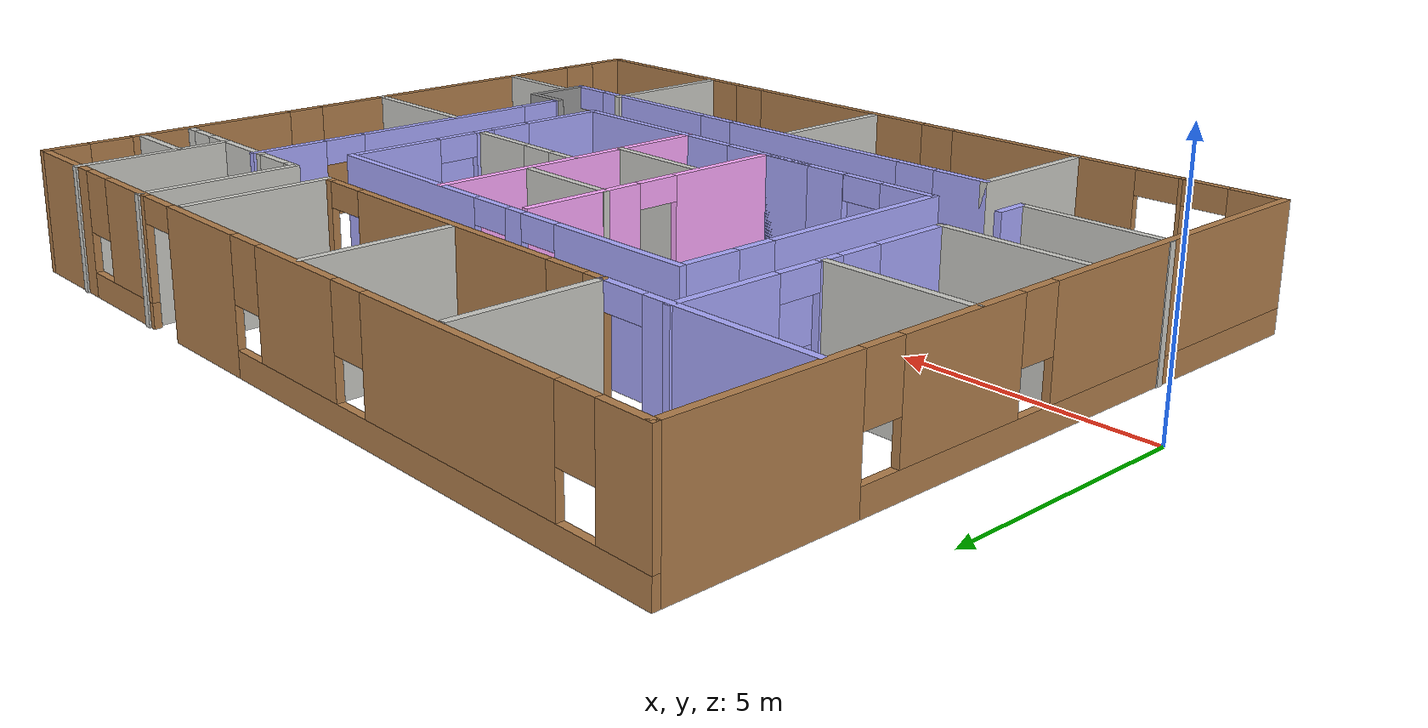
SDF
<?xml version='1.0'?>
<sdf version='1.6'>
  <model name='newOffice'>
    <pose frame=''>10.3877 1.61821 0 0 -0 0</pose>
    <link name='Wall_0'>
      <pose frame=''>-8.92098 -0.018654 0 0 0 -1.5708</pose>
      <visual name='Wall_0_Visual_0'>
        <pose frame=''>-5.60223 0 1.25 0 -0 0</pose>
        <geometry>
          <box>
            <size>3.79554 0.15 2.5</size>
          </box>
        </geometry>
        <material>
          <script>
            <uri>file://media/materials/scripts/gazebo.material</uri>
            <name>Gazebo/Wood</name>
          </script>
          <ambient>1 0.666667 1 1</ambient>
        </material>
        <meta>
          <layer>0</layer>
        </meta>
      </visual>
      <collision name='Wall_0_Collision_0'>
        <geometry>
          <box>
            <size>3.79554 0.15 2.5</size>
          </box>
        </geometry>
        <pose frame=''>-5.60223 0 1.25 0 -0 0</pose>
      </collision>
      <visual name='Wall_0_Visual_1'>
        <pose frame=''>1.89777 0 0.25 0 -0 0</pose>
        <geometry>
          <box>
            <size>11.2045 0.15 0.5</size>
          </box>
        </geometry>
        <material>
          <script>
            <uri>file://media/materials/scripts/gazebo.material</uri>
            <name>Gazebo/Wood</name>
          </script>
          <ambient>1 0.666667 1 1</ambient>
        </material>
        <meta>
          <layer>0</layer>
        </meta>
      </visual>
      <collision name='Wall_0_Collision_1'>
        <geometry>
          <box>
            <size>11.2045 0.15 0.5</size>
          </box>
        </geometry>
        <pose frame=''>1.89777 0 0.25 0 -0 0</pose>
      </collision>
      <visual name='Wall_0_Visual_2'>
        <pose frame=''>-1.54552 0 1.5 0 -0 0</pose>
        <geometry>
          <box>
            <size>2.71788 0.15 2</size>
          </box>
        </geometry>
        <material>
          <script>
            <uri>file://media/materials/scripts/gazebo.material</uri>
            <name>Gazebo/Wood</name>
          </script>
          <ambient>1 0.666667 1 1</ambient>
        </material>
        <meta>
          <layer>0</layer>
        </meta>
      </visual>
      <collision name='Wall_0_Collision_2'>
        <geometry>
          <box>
            <size>2.71788 0.15 2</size>
          </box>
        </geometry>
        <pose frame=''>-1.54552 0 1.5 0 -0 0</pose>
      </collision>
      <visual name='Wall_0_Visual_3'>
        <pose frame=''>4.05671 0 1.5 0 -0 0</pose>
        <geometry>
          <box>
            <size>6.88658 0.15 2</size>
          </box>
        </geometry>
        <material>
          <script>
            <uri>file://media/materials/scripts/gazebo.material</uri>
            <name>Gazebo/Wood</name>
          </script>
          <ambient>1 0.666667 1 1</ambient>
        </material>
        <meta>
          <layer>0</layer>
        </meta>
      </visual>
      <collision name='Wall_0_Collision_3'>
        <geometry>
          <box>
            <size>6.88658 0.15 2</size>
          </box>
        </geometry>
        <pose frame=''>4.05671 0 1.5 0 -0 0</pose>
      </collision>
      <visual name='Wall_0_Visual_4'>
        <pose frame=''>-3.30446 0 1.9 0 -0 0</pose>
        <geometry>
          <box>
            <size>0.8 0.15 1.2</size>
          </box>
        </geometry>
        <material>
          <script>
            <uri>file://media/materials/scripts/gazebo.material</uri>
            <name>Gazebo/Wood</name>
          </script>
          <ambient>1 0.666667 1 1</ambient>
        </material>
        <meta>
          <layer>0</layer>
        </meta>
      </visual>
      <collision name='Wall_0_Collision_4'>
        <geometry>
          <box>
            <size>0.8 0.15 1.2</size>
          </box>
        </geometry>
        <pose frame=''>-3.30446 0 1.9 0 -0 0</pose>
      </collision>
      <visual name='Wall_0_Visual_5'>
        <pose frame=''>0.213419 0 1.9 0 -0 0</pose>
        <geometry>
          <box>
            <size>0.8 0.15 1.2</size>
          </box>
        </geometry>
        <material>
          <script>
            <uri>file://media/materials/scripts/gazebo.material</uri>
            <name>Gazebo/Wood</name>
          </script>
          <ambient>1 0.666667 1 1</ambient>
        </material>
        <meta>
          <layer>0</layer>
        </meta>
      </visual>
      <collision name='Wall_0_Collision_5'>
        <geometry>
          <box>
            <size>0.8 0.15 1.2</size>
          </box>
        </geometry>
        <pose frame=''>0.213419 0 1.9 0 -0 0</pose>
      </collision>
    </link>
    <link name='Wall_1'>
      <pose frame=''>0.004022 -7.44365 0 0 -0 0</pose>
      <visual name='Wall_1_Visual_0'>
        <pose frame=''>-8.45097 0 1.25 0 -0 0</pose>
        <geometry>
          <box>
            <size>1.09805 0.15 2.5</size>
          </box>
        </geometry>
        <material>
          <script>
            <uri>file://media/materials/scripts/gazebo.material</uri>
            <name>Gazebo/Wood</name>
          </script>
          <ambient>1 0.666667 1 1</ambient>
        </material>
        <meta>
          <layer>0</layer>
        </meta>
      </visual>
      <collision name='Wall_1_Collision_0'>
        <geometry>
          <box>
            <size>1.09805 0.15 2.5</size>
          </box>
        </geometry>
        <pose frame=''>-8.45097 0 1.25 0 -0 0</pose>
      </collision>
      <visual name='Wall_1_Visual_1'>
        <pose frame=''>-6.96251 0 1.25 0 -0 0</pose>
        <geometry>
          <box>
            <size>0.078887 0.15 2.5</size>
          </box>
        </geometry>
        <material>
          <script>
            <uri>file://media/materials/scripts/gazebo.material</uri>
            <name>Gazebo/Wood</name>
          </script>
          <ambient>1 0.666667 1 1</ambient>
        </material>
        <meta>
          <layer>0</layer>
        </meta>
      </visual>
      <collision name='Wall_1_Collision_1'>
        <geometry>
          <box>
            <size>0.078887 0.15 2.5</size>
          </box>
        </geometry>
        <pose frame=''>-6.96251 0 1.25 0 -0 0</pose>
      </collision>
      <visual name='Wall_1_Visual_2'>
        <pose frame=''>-3.87848 0 1.25 0 -0 0</pose>
        <geometry>
          <box>
            <size>4.28916 0.15 2.5</size>
          </box>
        </geometry>
        <material>
          <script>
            <uri>file://media/materials/scripts/gazebo.material</uri>
            <name>Gazebo/Wood</name>
          </script>
          <ambient>1 0.666667 1 1</ambient>
        </material>
        <meta>
          <layer>0</layer>
        </meta>
      </visual>
      <collision name='Wall_1_Collision_2'>
        <geometry>
          <box>
            <size>4.28916 0.15 2.5</size>
          </box>
        </geometry>
        <pose frame=''>-3.87848 0 1.25 0 -0 0</pose>
      </collision>
      <visual name='Wall_1_Visual_3'>
        <pose frame=''>3.63305 0 0.25 0 -0 0</pose>
        <geometry>
          <box>
            <size>10.7339 0.15 0.5</size>
          </box>
        </geometry>
        <material>
          <script>
            <uri>file://media/materials/scripts/gazebo.material</uri>
            <name>Gazebo/Wood</name>
          </script>
          <ambient>1 0.666667 1 1</ambient>
        </material>
        <meta>
          <layer>0</layer>
        </meta>
      </visual>
      <collision name='Wall_1_Collision_3'>
        <geometry>
          <box>
            <size>10.7339 0.15 0.5</size>
          </box>
        </geometry>
        <pose frame=''>3.63305 0 0.25 0 -0 0</pose>
      </collision>
      <visual name='Wall_1_Visual_4'>
        <pose frame=''>1.41922 0 1.5 0 -0 0</pose>
        <geometry>
          <box>
            <size>4.70624 0.15 2</size>
          </box>
        </geometry>
        <material>
          <script>
            <uri>file://media/materials/scripts/gazebo.material</uri>
            <name>Gazebo/Wood</name>
          </script>
          <ambient>1 0.666667 1 1</ambient>
        </material>
        <meta>
          <layer>0</layer>
        </meta>
      </visual>
      <collision name='Wall_1_Collision_4'>
        <geometry>
          <box>
            <size>4.70624 0.15 2</size>
          </box>
        </geometry>
        <pose frame=''>1.41922 0 1.5 0 -0 0</pose>
      </collision>
      <visual name='Wall_1_Visual_5'>
        <pose frame=''>6.78617 0 1.5 0 -0 0</pose>
        <geometry>
          <box>
            <size>4.42766 0.15 2</size>
          </box>
        </geometry>
        <material>
          <script>
            <uri>file://media/materials/scripts/gazebo.material</uri>
            <name>Gazebo/Wood</name>
          </script>
          <ambient>1 0.666667 1 1</ambient>
        </material>
        <meta>
          <layer>0</layer>
        </meta>
      </visual>
      <collision name='Wall_1_Collision_5'>
        <geometry>
          <box>
            <size>4.42766 0.15 2</size>
          </box>
        </geometry>
        <pose frame=''>6.78617 0 1.5 0 -0 0</pose>
      </collision>
      <visual name='Wall_1_Visual_6'>
        <pose frame=''>-1.3339 0 1.9 0 -0 0</pose>
        <geometry>
          <box>
            <size>0.8 0.15 1.2</size>
          </box>
        </geometry>
        <material>
          <script>
            <uri>file://media/materials/scripts/gazebo.material</uri>
            <name>Gazebo/Wood</name>
          </script>
          <ambient>1 0.666667 1 1</ambient>
        </material>
        <meta>
          <layer>0</layer>
        </meta>
      </visual>
      <collision name='Wall_1_Collision_6'>
        <geometry>
          <box>
            <size>0.8 0.15 1.2</size>
          </box>
        </geometry>
        <pose frame=''>-1.3339 0 1.9 0 -0 0</pose>
      </collision>
      <visual name='Wall_1_Visual_7'>
        <pose frame=''>4.17234 0 1.9 0 -0 0</pose>
        <geometry>
          <box>
            <size>0.8 0.15 1.2</size>
          </box>
        </geometry>
        <material>
          <script>
            <uri>file://media/materials/scripts/gazebo.material</uri>
            <name>Gazebo/Wood</name>
          </script>
          <ambient>1 0.666667 1 1</ambient>
        </material>
        <meta>
          <layer>0</layer>
        </meta>
      </visual>
      <collision name='Wall_1_Collision_7'>
        <geometry>
          <box>
            <size>0.8 0.15 1.2</size>
          </box>
        </geometry>
        <pose frame=''>4.17234 0 1.9 0 -0 0</pose>
      </collision>
      <visual name='Wall_1_Visual_8'>
        <pose frame=''>-7.45195 0 2.25 0 -0 0</pose>
        <geometry>
          <box>
            <size>0.9 0.15 0.5</size>
          </box>
        </geometry>
        <material>
          <script>
            <uri>file://media/materials/scripts/gazebo.material</uri>
            <name>Gazebo/Wood</name>
          </script>
          <ambient>1 0.666667 1 1</ambient>
        </material>
        <meta>
          <layer>0</layer>
        </meta>
      </visual>
      <collision name='Wall_1_Collision_8'>
        <geometry>
          <box>
            <size>0.9 0.15 0.5</size>
          </box>
        </geometry>
        <pose frame=''>-7.45195 0 2.25 0 -0 0</pose>
      </collision>
      <visual name='Wall_1_Visual_9'>
        <pose frame=''>-6.47306 0 2.25 0 -0 0</pose>
        <geometry>
          <box>
            <size>0.9 0.15 0.5</size>
          </box>
        </geometry>
        <material>
          <script>
            <uri>file://media/materials/scripts/gazebo.material</uri>
            <name>Gazebo/Wood</name>
          </script>
          <ambient>1 0.666667 1 1</ambient>
        </material>
        <meta>
          <layer>0</layer>
        </meta>
      </visual>
      <collision name='Wall_1_Collision_9'>
        <geometry>
          <box>
            <size>0.9 0.15 0.5</size>
          </box>
        </geometry>
        <pose frame=''>-6.47306 0 2.25 0 -0 0</pose>
      </collision>
    </link>
    <link name='Wall_11'>
      <collision name='Wall_11_Collision'>
        <geometry>
          <box>
            <size>3 0.15 2.5</size>
          </box>
        </geometry>
        <pose frame=''>0 0 1.25 0 -0 0</pose>
      </collision>
      <visual name='Wall_11_Visual'>
        <pose frame=''>0 0 1.25 0 -0 0</pose>
        <geometry>
          <box>
            <size>3 0.15 2.5</size>
          </box>
        </geometry>
        <material>
          <script>
            <uri>file://media/materials/scripts/gazebo.material</uri>
            <name>Gazebo/CeilingTiled</name>
          </script>
          <ambient>0.760784 0.662745 0.627451 1</ambient>
        </material>
        <meta>
          <layer>0</layer>
        </meta>
      </visual>
      <pose frame=''>-0.660428 5.89112 0 0 -0 1.5708</pose>
    </link>
    <link name='Wall_13'>
      <collision name='Wall_13_Collision'>
        <geometry>
          <box>
            <size>3.25 0.15 2.5</size>
          </box>
        </geometry>
        <pose frame=''>0 0 1.25 0 -0 0</pose>
      </collision>
      <visual name='Wall_13_Visual'>
        <pose frame=''>0 0 1.25 0 -0 0</pose>
        <geometry>
          <box>
            <size>3.25 0.15 2.5</size>
          </box>
        </geometry>
        <material>
          <script>
            <uri>file://media/materials/scripts/gazebo.material</uri>
            <name>Gazebo/CeilingTiled</name>
          </script>
          <ambient>0.760784 0.662745 0.627451 1</ambient>
        </material>
        <meta>
          <layer>0</layer>
        </meta>
      </visual>
      <pose frame=''>4.6433 5.89365 0 0 0 -1.5708</pose>
    </link>
    <link name='Wall_14'>
      <pose frame=''>6.6933 4.34365 0 0 -0 0</pose>
      <visual name='Wall_14_Visual_0'>
        <pose frame=''>-1.94946 0 1.25 0 -0 0</pose>
        <geometry>
          <box>
            <size>0.351082 0.15 2.5</size>
          </box>
        </geometry>
        <material>
          <script>
            <uri>file://media/materials/scripts/gazebo.material</uri>
            <name>Gazebo/CeilingTiled</name>
          </script>
          <ambient>0.760784 0.662745 0.627451 1</ambient>
        </material>
        <meta>
          <layer>0</layer>
        </meta>
      </visual>
      <collision name='Wall_14_Collision_0'>
        <geometry>
          <box>
            <size>0.351082 0.15 2.5</size>
          </box>
        </geometry>
        <pose frame=''>-1.94946 0 1.25 0 -0 0</pose>
      </collision>
      <visual name='Wall_14_Visual_1'>
        <pose frame=''>0.175003 0 1.25 0 -0 0</pose>
        <geometry>
          <box>
            <size>2.09784 0.15 2.5</size>
          </box>
        </geometry>
        <material>
          <script>
            <uri>file://media/materials/scripts/gazebo.material</uri>
            <name>Gazebo/CeilingTiled</name>
          </script>
          <ambient>0.760784 0.662745 0.627451 1</ambient>
        </material>
        <meta>
          <layer>0</layer>
        </meta>
      </visual>
      <collision name='Wall_14_Collision_1'>
        <geometry>
          <box>
            <size>2.09784 0.15 2.5</size>
          </box>
        </geometry>
        <pose frame=''>0.175003 0 1.25 0 -0 0</pose>
      </collision>
      <visual name='Wall_14_Visual_2'>
        <pose frame=''>1.98681 0 1.25 0 -0 0</pose>
        <geometry>
          <box>
            <size>0.276388 0.15 2.5</size>
          </box>
        </geometry>
        <material>
          <script>
            <uri>file://media/materials/scripts/gazebo.material</uri>
            <name>Gazebo/CeilingTiled</name>
          </script>
          <ambient>0.760784 0.662745 0.627451 1</ambient>
        </material>
        <meta>
          <layer>0</layer>
        </meta>
      </visual>
      <collision name='Wall_14_Collision_2'>
        <geometry>
          <box>
            <size>0.276388 0.15 2.5</size>
          </box>
        </geometry>
        <pose frame=''>1.98681 0 1.25 0 -0 0</pose>
      </collision>
      <visual name='Wall_14_Visual_3'>
        <pose frame=''>-1.32392 0 2.25 0 -0 0</pose>
        <geometry>
          <box>
            <size>0.9 0.15 0.5</size>
          </box>
        </geometry>
        <material>
          <script>
            <uri>file://media/materials/scripts/gazebo.material</uri>
            <name>Gazebo/CeilingTiled</name>
          </script>
          <ambient>0.760784 0.662745 0.627451 1</ambient>
        </material>
        <meta>
          <layer>0</layer>
        </meta>
      </visual>
      <collision name='Wall_14_Collision_3'>
        <geometry>
          <box>
            <size>0.9 0.15 0.5</size>
          </box>
        </geometry>
        <pose frame=''>-1.32392 0 2.25 0 -0 0</pose>
      </collision>
      <visual name='Wall_14_Visual_4'>
        <pose frame=''>1.53627 0 2.25 0 -0 0</pose>
        <geometry>
          <box>
            <size>0.624688 0.15 0.5</size>
          </box>
        </geometry>
        <material>
          <script>
            <uri>file://media/materials/scripts/gazebo.material</uri>
            <name>Gazebo/CeilingTiled</name>
          </script>
          <ambient>0.760784 0.662745 0.627451 1</ambient>
        </material>
        <meta>
          <layer>0</layer>
        </meta>
      </visual>
      <collision name='Wall_14_Collision_4'>
        <geometry>
          <box>
            <size>0.624688 0.15 0.5</size>
          </box>
        </geometry>
        <pose frame=''>1.53627 0 2.25 0 -0 0</pose>
      </collision>
    </link>
    <link name='Wall_16'>
      <collision name='Wall_16_Collision'>
        <geometry>
          <box>
            <size>3.25 0.15 2.5</size>
          </box>
        </geometry>
        <pose frame=''>0 0 1.25 0 -0 0</pose>
      </collision>
      <visual name='Wall_16_Visual'>
        <pose frame=''>0 0 1.25 0 -0 0</pose>
        <geometry>
          <box>
            <size>3.25 0.15 2.5</size>
          </box>
        </geometry>
        <material>
          <script>
            <uri>file://media/materials/scripts/gazebo.material</uri>
            <name>Gazebo/CeilingTiled</name>
          </script>
          <ambient>0.760784 0.662745 0.627451 1</ambient>
        </material>
        <meta>
          <layer>0</layer>
        </meta>
      </visual>
      <pose frame=''>7.29516 5.89365 0 0 0 -1.5708</pose>
    </link>
    <link name='Wall_18'>
      <collision name='Wall_18_Collision'>
        <geometry>
          <box>
            <size>1.75 0.15 2.5</size>
          </box>
        </geometry>
        <pose frame=''>0 0 1.25 0 -0 0</pose>
      </collision>
      <visual name='Wall_18_Visual'>
        <pose frame=''>0 0 1.25 0 -0 0</pose>
        <geometry>
          <box>
            <size>1.75 0.15 2.5</size>
          </box>
        </geometry>
        <material>
          <script>
            <uri>file://media/materials/scripts/gazebo.material</uri>
            <name>Gazebo/CeilingTiled</name>
          </script>
          <ambient>0.760784 0.662745 0.627451 1</ambient>
        </material>
        <meta>
          <layer>0</layer>
        </meta>
      </visual>
      <pose frame=''>8.14169 5.3966 0 0 -0 0</pose>
    </link>
    <link name='Wall_2'>
      <pose frame=''>8.92902 -0.018654 0 0 -0 1.5708</pose>
      <visual name='Wall_2_Visual_0'>
        <pose frame=''>-7.00867 0 1.25 0 -0 0</pose>
        <geometry>
          <box>
            <size>0.982667 0.15 2.5</size>
          </box>
        </geometry>
        <material>
          <script>
            <uri>file://media/materials/scripts/gazebo.material</uri>
            <name>Gazebo/Wood</name>
          </script>
          <ambient>1 0.666667 1 1</ambient>
        </material>
        <meta>
          <layer>0</layer>
        </meta>
      </visual>
      <collision name='Wall_2_Collision_0'>
        <geometry>
          <box>
            <size>0.982667 0.15 2.5</size>
          </box>
        </geometry>
        <pose frame=''>-7.00867 0 1.25 0 -0 0</pose>
      </collision>
      <visual name='Wall_2_Visual_1'>
        <pose frame=''>7.01908 0 1.25 0 -0 0</pose>
        <geometry>
          <box>
            <size>0.961832 0.15 2.5</size>
          </box>
        </geometry>
        <material>
          <script>
            <uri>file://media/materials/scripts/gazebo.material</uri>
            <name>Gazebo/Wood</name>
          </script>
          <ambient>1 0.666667 1 1</ambient>
        </material>
        <meta>
          <layer>0</layer>
        </meta>
      </visual>
      <collision name='Wall_2_Collision_1'>
        <geometry>
          <box>
            <size>0.961832 0.15 2.5</size>
          </box>
        </geometry>
        <pose frame=''>7.01908 0 1.25 0 -0 0</pose>
      </collision>
      <visual name='Wall_2_Visual_2'>
        <pose frame=''>-0.439582 0 0.25 0 -0 0</pose>
        <geometry>
          <box>
            <size>12.1555 0.15 0.5</size>
          </box>
        </geometry>
        <material>
          <script>
            <uri>file://media/materials/scripts/gazebo.material</uri>
            <name>Gazebo/Wood</name>
          </script>
          <ambient>1 0.666667 1 1</ambient>
        </material>
        <meta>
          <layer>0</layer>
        </meta>
      </visual>
      <collision name='Wall_2_Collision_2'>
        <geometry>
          <box>
            <size>12.1555 0.15 0.5</size>
          </box>
        </geometry>
        <pose frame=''>-0.439582 0 0.25 0 -0 0</pose>
      </collision>
      <visual name='Wall_2_Visual_3'>
        <pose frame=''>-2.24767 0 1.5 0 -0 0</pose>
        <geometry>
          <box>
            <size>6.93933 0.15 2</size>
          </box>
        </geometry>
        <material>
          <script>
            <uri>file://media/materials/scripts/gazebo.material</uri>
            <name>Gazebo/Wood</name>
          </script>
          <ambient>1 0.666667 1 1</ambient>
        </material>
        <meta>
          <layer>0</layer>
        </meta>
      </visual>
      <collision name='Wall_2_Collision_3'>
        <geometry>
          <box>
            <size>6.93933 0.15 2</size>
          </box>
        </geometry>
        <pose frame=''>-2.24767 0 1.5 0 -0 0</pose>
      </collision>
      <visual name='Wall_2_Visual_4'>
        <pose frame=''>3.83008 0 1.5 0 -0 0</pose>
        <geometry>
          <box>
            <size>3.61617 0.15 2</size>
          </box>
        </geometry>
        <material>
          <script>
            <uri>file://media/materials/scripts/gazebo.material</uri>
            <name>Gazebo/Wood</name>
          </script>
          <ambient>1 0.666667 1 1</ambient>
        </material>
        <meta>
          <layer>0</layer>
        </meta>
      </visual>
      <collision name='Wall_2_Collision_4'>
        <geometry>
          <box>
            <size>3.61617 0.15 2</size>
          </box>
        </geometry>
        <pose frame=''>3.83008 0 1.5 0 -0 0</pose>
      </collision>
      <visual name='Wall_2_Visual_5'>
        <pose frame=''>-6.11733 0 1.9 0 -0 0</pose>
        <geometry>
          <box>
            <size>0.8 0.15 1.2</size>
          </box>
        </geometry>
        <material>
          <script>
            <uri>file://media/materials/scripts/gazebo.material</uri>
            <name>Gazebo/Wood</name>
          </script>
          <ambient>1 0.666667 1 1</ambient>
        </material>
        <meta>
          <layer>0</layer>
        </meta>
      </visual>
      <collision name='Wall_2_Collision_5'>
        <geometry>
          <box>
            <size>0.8 0.15 1.2</size>
          </box>
        </geometry>
        <pose frame=''>-6.11733 0 1.9 0 -0 0</pose>
      </collision>
      <visual name='Wall_2_Visual_6'>
        <pose frame=''>1.622 0 1.9 0 -0 0</pose>
        <geometry>
          <box>
            <size>0.8 0.15 1.2</size>
          </box>
        </geometry>
        <material>
          <script>
            <uri>file://media/materials/scripts/gazebo.material</uri>
            <name>Gazebo/Wood</name>
          </script>
          <ambient>1 0.666667 1 1</ambient>
        </material>
        <meta>
          <layer>0</layer>
        </meta>
      </visual>
      <collision name='Wall_2_Collision_6'>
        <geometry>
          <box>
            <size>0.8 0.15 1.2</size>
          </box>
        </geometry>
        <pose frame=''>1.622 0 1.9 0 -0 0</pose>
      </collision>
      <visual name='Wall_2_Visual_7'>
        <pose frame=''>6.08817 0 2.25 0 -0 0</pose>
        <geometry>
          <box>
            <size>0.9 0.15 0.5</size>
          </box>
        </geometry>
        <material>
          <script>
            <uri>file://media/materials/scripts/gazebo.material</uri>
            <name>Gazebo/Wood</name>
          </script>
          <ambient>1 0.666667 1 1</ambient>
        </material>
        <meta>
          <layer>0</layer>
        </meta>
      </visual>
      <collision name='Wall_2_Collision_7'>
        <geometry>
          <box>
            <size>0.9 0.15 0.5</size>
          </box>
        </geometry>
        <pose frame=''>6.08817 0 2.25 0 -0 0</pose>
      </collision>
    </link>
    <link name='Wall_20'>
      <pose frame=''>-5.96415 1.3696 0 0 0 -1.5708</pose>
      <visual name='Wall_20_Visual_0'>
        <pose frame=''>-1.99614 0 1.25 0 -0 0</pose>
        <geometry>
          <box>
            <size>2.25772 0.15 2.5</size>
          </box>
        </geometry>
        <material>
          <script>
            <uri>file://media/materials/scripts/gazebo.material</uri>
            <name>Gazebo/Grey</name>
          </script>
          <ambient>0.666667 0.666667 1 1</ambient>
        </material>
        <meta>
          <layer>0</layer>
        </meta>
      </visual>
      <collision name='Wall_20_Collision_0'>
        <geometry>
          <box>
            <size>2.25772 0.15 2.5</size>
          </box>
        </geometry>
        <pose frame=''>-1.99614 0 1.25 0 -0 0</pose>
      </collision>
      <visual name='Wall_20_Visual_1'>
        <pose frame=''>0.286292 0 1.25 0 -0 0</pose>
        <geometry>
          <box>
            <size>0.507151 0.15 2.5</size>
          </box>
        </geometry>
        <material>
          <script>
            <uri>file://media/materials/scripts/gazebo.material</uri>
            <name>Gazebo/Grey</name>
          </script>
          <ambient>0.666667 0.666667 1 1</ambient>
        </material>
        <meta>
          <layer>0</layer>
        </meta>
      </visual>
      <collision name='Wall_20_Collision_1'>
        <geometry>
          <box>
            <size>0.507151 0.15 2.5</size>
          </box>
        </geometry>
        <pose frame=''>0.286292 0 1.25 0 -0 0</pose>
      </collision>
      <visual name='Wall_20_Visual_2'>
        <pose frame=''>2.28243 0 1.25 0 -0 0</pose>
        <geometry>
          <box>
            <size>1.68513 0.15 2.5</size>
          </box>
        </geometry>
        <material>
          <script>
            <uri>file://media/materials/scripts/gazebo.material</uri>
            <name>Gazebo/Grey</name>
          </script>
          <ambient>0.666667 0.666667 1 1</ambient>
        </material>
        <meta>
          <layer>0</layer>
        </meta>
      </visual>
      <collision name='Wall_20_Collision_2'>
        <geometry>
          <box>
            <size>1.68513 0.15 2.5</size>
          </box>
        </geometry>
        <pose frame=''>2.28243 0 1.25 0 -0 0</pose>
      </collision>
      <visual name='Wall_20_Visual_3'>
        <pose frame=''>-0.417283 0 2.25 0 -0 0</pose>
        <geometry>
          <box>
            <size>0.9 0.15 0.5</size>
          </box>
        </geometry>
        <material>
          <script>
            <uri>file://media/materials/scripts/gazebo.material</uri>
            <name>Gazebo/Grey</name>
          </script>
          <ambient>0.666667 0.666667 1 1</ambient>
        </material>
        <meta>
          <layer>0</layer>
        </meta>
      </visual>
      <collision name='Wall_20_Collision_3'>
        <geometry>
          <box>
            <size>0.9 0.15 0.5</size>
          </box>
        </geometry>
        <pose frame=''>-0.417283 0 2.25 0 -0 0</pose>
      </collision>
      <visual name='Wall_20_Visual_4'>
        <pose frame=''>0.989867 0 2.25 0 -0 0</pose>
        <geometry>
          <box>
            <size>0.9 0.15 0.5</size>
          </box>
        </geometry>
        <material>
          <script>
            <uri>file://media/materials/scripts/gazebo.material</uri>
            <name>Gazebo/Grey</name>
          </script>
          <ambient>0.666667 0.666667 1 1</ambient>
        </material>
        <meta>
          <layer>0</layer>
        </meta>
      </visual>
      <collision name='Wall_20_Collision_4'>
        <geometry>
          <box>
            <size>0.9 0.15 0.5</size>
          </box>
        </geometry>
        <pose frame=''>0.989867 0 2.25 0 -0 0</pose>
      </collision>
    </link>
    <link name='Wall_21'>
      <collision name='Wall_21_Collision'>
        <geometry>
          <box>
            <size>3 0.15 2.5</size>
          </box>
        </geometry>
        <pose frame=''>0 0 1.25 0 -0 0</pose>
      </collision>
      <visual name='Wall_21_Visual'>
        <pose frame=''>0 0 1.25 0 -0 0</pose>
        <geometry>
          <box>
            <size>3 0.15 2.5</size>
          </box>
        </geometry>
        <material>
          <script>
            <uri>file://media/materials/scripts/gazebo.material</uri>
            <name>Gazebo/CeilingTiled</name>
          </script>
          <ambient>0.760784 0.662745 0.627451 1</ambient>
        </material>
        <meta>
          <layer>0</layer>
        </meta>
      </visual>
      <pose frame=''>-7.38915 -1.6804 0 0 -0 3.14159</pose>
    </link>
    <link name='Wall_23'>
      <collision name='Wall_23_Collision'>
        <geometry>
          <box>
            <size>3 0.15 2.5</size>
          </box>
        </geometry>
        <pose frame=''>0 0 1.25 0 -0 0</pose>
      </collision>
      <visual name='Wall_23_Visual'>
        <pose frame=''>0 0 1.25 0 -0 0</pose>
        <geometry>
          <box>
            <size>3 0.15 2.5</size>
          </box>
        </geometry>
        <material>
          <script>
            <uri>file://media/materials/scripts/gazebo.material</uri>
            <name>Gazebo/CeilingTiled</name>
          </script>
          <ambient>0.760784 0.662745 0.627451 1</ambient>
        </material>
        <meta>
          <layer>0</layer>
        </meta>
      </visual>
      <pose frame=''>-7.47016 1.20945 0 0 -0 0</pose>
    </link>
    <link name='Wall_25'>
      <collision name='Wall_25_Collision'>
        <geometry>
          <box>
            <size>3 0.15 2.5</size>
          </box>
        </geometry>
        <pose frame=''>0 0 1.25 0 -0 0</pose>
      </collision>
      <visual name='Wall_25_Visual'>
        <pose frame=''>0 0 1.25 0 -0 0</pose>
        <geometry>
          <box>
            <size>3 0.15 2.5</size>
          </box>
        </geometry>
        <material>
          <script>
            <uri>file://media/materials/scripts/gazebo.material</uri>
            <name>Gazebo/CeilingTiled</name>
          </script>
          <ambient>0.760784 0.662745 0.627451 1</ambient>
        </material>
        <meta>
          <layer>0</layer>
        </meta>
      </visual>
      <pose frame=''>-7.51668 -3.72208 0 0 -0 0</pose>
    </link>
    <link name='Wall_26'>
      <collision name='Wall_26_Collision'>
        <geometry>
          <box>
            <size>0.75 0.15 2.5</size>
          </box>
        </geometry>
        <pose frame=''>0 0 1.25 0 -0 0</pose>
      </collision>
      <visual name='Wall_26_Visual'>
        <pose frame=''>0 0 1.25 0 -0 0</pose>
        <geometry>
          <box>
            <size>0.75 0.15 2.5</size>
          </box>
        </geometry>
        <material>
          <script>
            <uri>file://media/materials/scripts/gazebo.material</uri>
            <name>Gazebo/Grey</name>
          </script>
          <ambient>0.666667 0.666667 1 1</ambient>
        </material>
        <meta>
          <layer>0</layer>
        </meta>
      </visual>
      <pose frame=''>-6.09169 -3.42209 0 0 -0 1.5708</pose>
    </link>
    <link name='Wall_28'>
      <pose frame=''>-4.70801 0.020406 0 0 0 -1.5708</pose>
      <visual name='Wall_28_Visual_0'>
        <pose frame=''>-2.47749 0 1.25 0 -0 0</pose>
        <geometry>
          <box>
            <size>1.29502 0.15 2.5</size>
          </box>
        </geometry>
        <material>
          <script>
            <uri>file://media/materials/scripts/gazebo.material</uri>
            <name>Gazebo/Grey</name>
          </script>
          <ambient>0.666667 0.666667 1 1</ambient>
        </material>
        <meta>
          <layer>0</layer>
        </meta>
      </visual>
      <collision name='Wall_28_Collision_0'>
        <geometry>
          <box>
            <size>1.29502 0.15 2.5</size>
          </box>
        </geometry>
        <pose frame=''>-2.47749 0 1.25 0 -0 0</pose>
      </collision>
      <visual name='Wall_28_Visual_1'>
        <pose frame=''>0.647508 0 0.25 0 -0 0</pose>
        <geometry>
          <box>
            <size>4.95498 0.15 0.5</size>
          </box>
        </geometry>
        <material>
          <script>
            <uri>file://media/materials/scripts/gazebo.material</uri>
            <name>Gazebo/Grey</name>
          </script>
          <ambient>0.666667 0.666667 1 1</ambient>
        </material>
        <meta>
          <layer>0</layer>
        </meta>
      </visual>
      <collision name='Wall_28_Collision_1'>
        <geometry>
          <box>
            <size>4.95498 0.15 0.5</size>
          </box>
        </geometry>
        <pose frame=''>0.647508 0 0.25 0 -0 0</pose>
      </collision>
      <visual name='Wall_28_Visual_2'>
        <pose frame=''>1.04751 0 1.5 0 -0 0</pose>
        <geometry>
          <box>
            <size>4.15498 0.15 2</size>
          </box>
        </geometry>
        <material>
          <script>
            <uri>file://media/materials/scripts/gazebo.material</uri>
            <name>Gazebo/Grey</name>
          </script>
          <ambient>0.666667 0.666667 1 1</ambient>
        </material>
        <meta>
          <layer>0</layer>
        </meta>
      </visual>
      <collision name='Wall_28_Collision_2'>
        <geometry>
          <box>
            <size>4.15498 0.15 2</size>
          </box>
        </geometry>
        <pose frame=''>1.04751 0 1.5 0 -0 0</pose>
      </collision>
      <visual name='Wall_28_Visual_3'>
        <pose frame=''>-1.42998 0 1.9 0 -0 0</pose>
        <geometry>
          <box>
            <size>0.8 0.15 1.2</size>
          </box>
        </geometry>
        <material>
          <script>
            <uri>file://media/materials/scripts/gazebo.material</uri>
            <name>Gazebo/Grey</name>
          </script>
          <ambient>0.666667 0.666667 1 1</ambient>
        </material>
        <meta>
          <layer>0</layer>
        </meta>
      </visual>
      <collision name='Wall_28_Collision_3'>
        <geometry>
          <box>
            <size>0.8 0.15 1.2</size>
          </box>
        </geometry>
        <pose frame=''>-1.42998 0 1.9 0 -0 0</pose>
      </collision>
    </link>
    <link name='Wall_29'>
      <pose frame=''>-2.65801 -3.02959 0 0 -0 0</pose>
      <visual name='Wall_29_Visual_0'>
        <pose frame=''>-1.51055 0 1.25 0 -0 0</pose>
        <geometry>
          <box>
            <size>1.2289 0.15 2.5</size>
          </box>
        </geometry>
        <material>
          <script>
            <uri>file://media/materials/scripts/gazebo.material</uri>
            <name>Gazebo/Grey</name>
          </script>
          <ambient>0.666667 0.666667 1 1</ambient>
        </material>
        <meta>
          <layer>0</layer>
        </meta>
      </visual>
      <collision name='Wall_29_Collision_0'>
        <geometry>
          <box>
            <size>1.2289 0.15 2.5</size>
          </box>
        </geometry>
        <pose frame=''>-1.51055 0 1.25 0 -0 0</pose>
      </collision>
      <visual name='Wall_29_Visual_1'>
        <pose frame=''>1.06445 0 1.25 0 -0 0</pose>
        <geometry>
          <box>
            <size>2.1211 0.15 2.5</size>
          </box>
        </geometry>
        <material>
          <script>
            <uri>file://media/materials/scripts/gazebo.material</uri>
            <name>Gazebo/Grey</name>
          </script>
          <ambient>0.666667 0.666667 1 1</ambient>
        </material>
        <meta>
          <layer>0</layer>
        </meta>
      </visual>
      <collision name='Wall_29_Collision_1'>
        <geometry>
          <box>
            <size>2.1211 0.15 2.5</size>
          </box>
        </geometry>
        <pose frame=''>1.06445 0 1.25 0 -0 0</pose>
      </collision>
      <visual name='Wall_29_Visual_2'>
        <pose frame=''>1.50801 0 1.25 0 -0 0</pose>
        <geometry>
          <box>
            <size>1.23399 0.15 2.5</size>
          </box>
        </geometry>
        <material>
          <script>
            <uri>file://media/materials/scripts/gazebo.material</uri>
            <name>Gazebo/Grey</name>
          </script>
          <ambient>0.666667 0.666667 1 1</ambient>
        </material>
        <meta>
          <layer>0</layer>
        </meta>
      </visual>
      <collision name='Wall_29_Collision_2'>
        <geometry>
          <box>
            <size>1.23399 0.15 2.5</size>
          </box>
        </geometry>
        <pose frame=''>1.50801 0 1.25 0 -0 0</pose>
      </collision>
      <visual name='Wall_29_Visual_3'>
        <pose frame=''>-0.452546 0 2.25 0 -0 0</pose>
        <geometry>
          <box>
            <size>0.887117 0.15 0.5</size>
          </box>
        </geometry>
        <material>
          <script>
            <uri>file://media/materials/scripts/gazebo.material</uri>
            <name>Gazebo/Grey</name>
          </script>
          <ambient>0.666667 0.666667 1 1</ambient>
        </material>
        <meta>
          <layer>0</layer>
        </meta>
      </visual>
      <collision name='Wall_29_Collision_3'>
        <geometry>
          <box>
            <size>0.887117 0.15 0.5</size>
          </box>
        </geometry>
        <pose frame=''>-0.452546 0 2.25 0 -0 0</pose>
      </collision>
    </link>
    <link name='Wall_3'>
      <pose frame=''>0.004022 7.40635 0 0 -0 3.14159</pose>
      <visual name='Wall_3_Visual_0'>
        <pose frame=''>-7.91801 0 1.25 0 -0 0</pose>
        <geometry>
          <box>
            <size>2.16398 0.15 2.5</size>
          </box>
        </geometry>
        <material>
          <script>
            <uri>file://media/materials/scripts/gazebo.material</uri>
            <name>Gazebo/Wood</name>
          </script>
          <ambient>1 0.666667 1 1</ambient>
        </material>
        <meta>
          <layer>0</layer>
        </meta>
      </visual>
      <collision name='Wall_3_Collision_0'>
        <geometry>
          <box>
            <size>2.16398 0.15 2.5</size>
          </box>
        </geometry>
        <pose frame=''>-7.91801 0 1.25 0 -0 0</pose>
      </collision>
      <visual name='Wall_3_Visual_1'>
        <pose frame=''>-2.4037 0 1.25 0 -0 0</pose>
        <geometry>
          <box>
            <size>2.2702 0.15 2.5</size>
          </box>
        </geometry>
        <material>
          <script>
            <uri>file://media/materials/scripts/gazebo.material</uri>
            <name>Gazebo/Wood</name>
          </script>
          <ambient>1 0.666667 1 1</ambient>
        </material>
        <meta>
          <layer>0</layer>
        </meta>
      </visual>
      <collision name='Wall_3_Collision_1'>
        <geometry>
          <box>
            <size>2.2702 0.15 2.5</size>
          </box>
        </geometry>
        <pose frame=''>-2.4037 0 1.25 0 -0 0</pose>
      </collision>
      <visual name='Wall_3_Visual_2'>
        <pose frame=''>-5.63741 0 0.25 0 -0 0</pose>
        <geometry>
          <box>
            <size>2.39722 0.15 0.5</size>
          </box>
        </geometry>
        <material>
          <script>
            <uri>file://media/materials/scripts/gazebo.material</uri>
            <name>Gazebo/Wood</name>
          </script>
          <ambient>1 0.666667 1 1</ambient>
        </material>
        <meta>
          <layer>0</layer>
        </meta>
      </visual>
      <collision name='Wall_3_Collision_2'>
        <geometry>
          <box>
            <size>2.39722 0.15 0.5</size>
          </box>
        </geometry>
        <pose frame=''>-5.63741 0 0.25 0 -0 0</pose>
      </collision>
      <visual name='Wall_3_Visual_3'>
        <pose frame=''>3.8657 0 0.25 0 -0 0</pose>
        <geometry>
          <box>
            <size>10.2686 0.15 0.5</size>
          </box>
        </geometry>
        <material>
          <script>
            <uri>file://media/materials/scripts/gazebo.material</uri>
            <name>Gazebo/Wood</name>
          </script>
          <ambient>1 0.666667 1 1</ambient>
        </material>
        <meta>
          <layer>0</layer>
        </meta>
      </visual>
      <collision name='Wall_3_Collision_3'>
        <geometry>
          <box>
            <size>10.2686 0.15 0.5</size>
          </box>
        </geometry>
        <pose frame=''>3.8657 0 0.25 0 -0 0</pose>
      </collision>
      <visual name='Wall_3_Visual_4'>
        <pose frame=''>-5.23741 0 1.5 0 -0 0</pose>
        <geometry>
          <box>
            <size>1.59722 0.15 2</size>
          </box>
        </geometry>
        <material>
          <script>
            <uri>file://media/materials/scripts/gazebo.material</uri>
            <name>Gazebo/Wood</name>
          </script>
          <ambient>1 0.666667 1 1</ambient>
        </material>
        <meta>
          <layer>0</layer>
        </meta>
      </visual>
      <collision name='Wall_3_Collision_4'>
        <geometry>
          <box>
            <size>1.59722 0.15 2</size>
          </box>
        </geometry>
        <pose frame=''>-5.23741 0 1.5 0 -0 0</pose>
      </collision>
      <visual name='Wall_3_Visual_5'>
        <pose frame=''>-5.23741 0 1.5 0 -0 0</pose>
        <geometry>
          <box>
            <size>1.59722 0.15 2</size>
          </box>
        </geometry>
        <material>
          <script>
            <uri>file://media/materials/scripts/gazebo.material</uri>
            <name>Gazebo/Wood</name>
          </script>
          <ambient>1 0.666667 1 1</ambient>
        </material>
        <meta>
          <layer>0</layer>
        </meta>
      </visual>
      <collision name='Wall_3_Collision_5'>
        <geometry>
          <box>
            <size>1.59722 0.15 2</size>
          </box>
        </geometry>
        <pose frame=''>-5.23741 0 1.5 0 -0 0</pose>
      </collision>
      <visual name='Wall_3_Visual_6'>
        <pose frame=''>0.676212 0 1.5 0 -0 0</pose>
        <geometry>
          <box>
            <size>2.28961 0.15 2</size>
          </box>
        </geometry>
        <material>
          <script>
            <uri>file://media/materials/scripts/gazebo.material</uri>
            <name>Gazebo/Wood</name>
          </script>
          <ambient>1 0.666667 1 1</ambient>
        </material>
        <meta>
          <layer>0</layer>
        </meta>
      </visual>
      <collision name='Wall_3_Collision_6'>
        <geometry>
          <box>
            <size>2.28961 0.15 2</size>
          </box>
        </geometry>
        <pose frame=''>0.676212 0 1.5 0 -0 0</pose>
      </collision>
      <visual name='Wall_3_Visual_7'>
        <pose frame=''>4.88237 0 1.5 0 -0 0</pose>
        <geometry>
          <box>
            <size>4.5227 0.15 2</size>
          </box>
        </geometry>
        <material>
          <script>
            <uri>file://media/materials/scripts/gazebo.material</uri>
            <name>Gazebo/Wood</name>
          </script>
          <ambient>1 0.666667 1 1</ambient>
        </material>
        <meta>
          <layer>0</layer>
        </meta>
      </visual>
      <collision name='Wall_3_Collision_7'>
        <geometry>
          <box>
            <size>4.5227 0.15 2</size>
          </box>
        </geometry>
        <pose frame=''>4.88237 0 1.5 0 -0 0</pose>
      </collision>
      <visual name='Wall_3_Visual_8'>
        <pose frame=''>8.47186 0 1.5 0 -0 0</pose>
        <geometry>
          <box>
            <size>1.05628 0.15 2</size>
          </box>
        </geometry>
        <material>
          <script>
            <uri>file://media/materials/scripts/gazebo.material</uri>
            <name>Gazebo/Wood</name>
          </script>
          <ambient>1 0.666667 1 1</ambient>
        </material>
        <meta>
          <layer>0</layer>
        </meta>
      </visual>
      <collision name='Wall_3_Collision_8'>
        <geometry>
          <box>
            <size>1.05628 0.15 2</size>
          </box>
        </geometry>
        <pose frame=''>8.47186 0 1.5 0 -0 0</pose>
      </collision>
      <visual name='Wall_3_Visual_9'>
        <pose frame=''>-6.43602 0 1.9 0 -0 0</pose>
        <geometry>
          <box>
            <size>0.8 0.15 1.2</size>
          </box>
        </geometry>
        <material>
          <script>
            <uri>file://media/materials/scripts/gazebo.material</uri>
            <name>Gazebo/Wood</name>
          </script>
          <ambient>1 0.666667 1 1</ambient>
        </material>
        <meta>
          <layer>0</layer>
        </meta>
      </visual>
      <collision name='Wall_3_Collision_9'>
        <geometry>
          <box>
            <size>0.8 0.15 1.2</size>
          </box>
        </geometry>
        <pose frame=''>-6.43602 0 1.9 0 -0 0</pose>
      </collision>
      <visual name='Wall_3_Visual_10'>
        <pose frame=''>-0.868594 0 1.9 0 -0 0</pose>
        <geometry>
          <box>
            <size>0.8 0.15 1.2</size>
          </box>
        </geometry>
        <material>
          <script>
            <uri>file://media/materials/scripts/gazebo.material</uri>
            <name>Gazebo/Wood</name>
          </script>
          <ambient>1 0.666667 1 1</ambient>
        </material>
        <meta>
          <layer>0</layer>
        </meta>
      </visual>
      <collision name='Wall_3_Collision_10'>
        <geometry>
          <box>
            <size>0.8 0.15 1.2</size>
          </box>
        </geometry>
        <pose frame=''>-0.868594 0 1.9 0 -0 0</pose>
      </collision>
      <visual name='Wall_3_Visual_11'>
        <pose frame=''>2.22102 0 1.9 0 -0 0</pose>
        <geometry>
          <box>
            <size>0.8 0.15 1.2</size>
          </box>
        </geometry>
        <material>
          <script>
            <uri>file://media/materials/scripts/gazebo.material</uri>
            <name>Gazebo/Wood</name>
          </script>
          <ambient>1 0.666667 1 1</ambient>
        </material>
        <meta>
          <layer>0</layer>
        </meta>
      </visual>
      <collision name='Wall_3_Collision_11'>
        <geometry>
          <box>
            <size>0.8 0.15 1.2</size>
          </box>
        </geometry>
        <pose frame=''>2.22102 0 1.9 0 -0 0</pose>
      </collision>
      <visual name='Wall_3_Visual_12'>
        <pose frame=''>7.54372 0 1.9 0 -0 0</pose>
        <geometry>
          <box>
            <size>0.8 0.15 1.2</size>
          </box>
        </geometry>
        <material>
          <script>
            <uri>file://media/materials/scripts/gazebo.material</uri>
            <name>Gazebo/Wood</name>
          </script>
          <ambient>1 0.666667 1 1</ambient>
        </material>
        <meta>
          <layer>0</layer>
        </meta>
      </visual>
      <collision name='Wall_3_Collision_12'>
        <geometry>
          <box>
            <size>0.8 0.15 1.2</size>
          </box>
        </geometry>
        <pose frame=''>7.54372 0 1.9 0 -0 0</pose>
      </collision>
      <visual name='Wall_3_Visual_13'>
        <pose frame=''>-3.9888 0 2.25 0 -0 0</pose>
        <geometry>
          <box>
            <size>0.9 0.15 0.5</size>
          </box>
        </geometry>
        <material>
          <script>
            <uri>file://media/materials/scripts/gazebo.material</uri>
            <name>Gazebo/Wood</name>
          </script>
          <ambient>1 0.666667 1 1</ambient>
        </material>
        <meta>
          <layer>0</layer>
        </meta>
      </visual>
      <collision name='Wall_3_Collision_13'>
        <geometry>
          <box>
            <size>0.9 0.15 0.5</size>
          </box>
        </geometry>
        <pose frame=''>-3.9888 0 2.25 0 -0 0</pose>
      </collision>
      <visual name='Wall_3_Visual_14'>
        <pose frame=''>-3.9888 0 2.25 0 -0 0</pose>
        <geometry>
          <box>
            <size>0.9 0.15 0.5</size>
          </box>
        </geometry>
        <material>
          <script>
            <uri>file://media/materials/scripts/gazebo.material</uri>
            <name>Gazebo/Wood</name>
          </script>
          <ambient>1 0.666667 1 1</ambient>
        </material>
        <meta>
          <layer>0</layer>
        </meta>
      </visual>
      <collision name='Wall_3_Collision_14'>
        <geometry>
          <box>
            <size>0.9 0.15 0.5</size>
          </box>
        </geometry>
        <pose frame=''>-3.9888 0 2.25 0 -0 0</pose>
      </collision>
    </link>
    <link name='Wall_30'>
      <pose frame=''>-0.60801 -0.104594 0 0 -0 1.5708</pose>
      <visual name='Wall_30_Visual_0'>
        <pose frame=''>-1.74285 0 1.25 0 -0 0</pose>
        <geometry>
          <box>
            <size>2.51429 0.15 2.5</size>
          </box>
        </geometry>
        <material>
          <script>
            <uri>file://media/materials/scripts/gazebo.material</uri>
            <name>Gazebo/Grey</name>
          </script>
          <ambient>1 0.666667 1 1</ambient>
        </material>
        <meta>
          <layer>0</layer>
        </meta>
      </visual>
      <collision name='Wall_30_Collision_0'>
        <geometry>
          <box>
            <size>2.51429 0.15 2.5</size>
          </box>
        </geometry>
        <pose frame=''>-1.74285 0 1.25 0 -0 0</pose>
      </collision>
      <visual name='Wall_30_Visual_1'>
        <pose frame=''>1.70715 0 1.25 0 -0 0</pose>
        <geometry>
          <box>
            <size>2.58571 0.15 2.5</size>
          </box>
        </geometry>
        <material>
          <script>
            <uri>file://media/materials/scripts/gazebo.material</uri>
            <name>Gazebo/Grey</name>
          </script>
          <ambient>1 0.666667 1 1</ambient>
        </material>
        <meta>
          <layer>0</layer>
        </meta>
      </visual>
      <collision name='Wall_30_Collision_1'>
        <geometry>
          <box>
            <size>2.58571 0.15 2.5</size>
          </box>
        </geometry>
        <pose frame=''>1.70715 0 1.25 0 -0 0</pose>
      </collision>
      <visual name='Wall_30_Visual_2'>
        <pose frame=''>-0.035708 0 2.25 0 -0 0</pose>
        <geometry>
          <box>
            <size>0.9 0.15 0.5</size>
          </box>
        </geometry>
        <material>
          <script>
            <uri>file://media/materials/scripts/gazebo.material</uri>
            <name>Gazebo/Grey</name>
          </script>
          <ambient>1 0.666667 1 1</ambient>
        </material>
        <meta>
          <layer>0</layer>
        </meta>
      </visual>
      <collision name='Wall_30_Collision_2'>
        <geometry>
          <box>
            <size>0.9 0.15 0.5</size>
          </box>
        </geometry>
        <pose frame=''>-0.035708 0 2.25 0 -0 0</pose>
      </collision>
    </link>
    <link name='Wall_32'>
      <pose frame=''>-0.033009 3.07041 0 0 -0 0</pose>
      <visual name='Wall_32_Visual_0'>
        <pose frame=''>-3.21785 0 1.25 0 -0 0</pose>
        <geometry>
          <box>
            <size>3.06431 0.15 2.5</size>
          </box>
        </geometry>
        <material>
          <script>
            <uri>file://media/materials/scripts/gazebo.material</uri>
            <name>Gazebo/Grey</name>
          </script>
          <ambient>0.666667 0.666667 1 1</ambient>
        </material>
        <meta>
          <layer>0</layer>
        </meta>
      </visual>
      <collision name='Wall_32_Collision_0'>
        <geometry>
          <box>
            <size>3.06431 0.15 2.5</size>
          </box>
        </geometry>
        <pose frame=''>-3.21785 0 1.25 0 -0 0</pose>
      </collision>
      <visual name='Wall_32_Visual_1'>
        <pose frame=''>-0.562706 0 1.25 0 -0 0</pose>
        <geometry>
          <box>
            <size>0.44597 0.15 2.5</size>
          </box>
        </geometry>
        <material>
          <script>
            <uri>file://media/materials/scripts/gazebo.material</uri>
            <name>Gazebo/Grey</name>
          </script>
          <ambient>0.666667 0.666667 1 1</ambient>
        </material>
        <meta>
          <layer>0</layer>
        </meta>
      </visual>
      <collision name='Wall_32_Collision_1'>
        <geometry>
          <box>
            <size>0.44597 0.15 2.5</size>
          </box>
        </geometry>
        <pose frame=''>-0.562706 0 1.25 0 -0 0</pose>
      </collision>
      <visual name='Wall_32_Visual_2'>
        <pose frame=''>2.65514 0 1.25 0 -0 0</pose>
        <geometry>
          <box>
            <size>4.18972 0.15 2.5</size>
          </box>
        </geometry>
        <material>
          <script>
            <uri>file://media/materials/scripts/gazebo.material</uri>
            <name>Gazebo/Grey</name>
          </script>
          <ambient>0.666667 0.666667 1 1</ambient>
        </material>
        <meta>
          <layer>0</layer>
        </meta>
      </visual>
      <collision name='Wall_32_Collision_2'>
        <geometry>
          <box>
            <size>4.18972 0.15 2.5</size>
          </box>
        </geometry>
        <pose frame=''>2.65514 0 1.25 0 -0 0</pose>
      </collision>
      <visual name='Wall_32_Visual_3'>
        <pose frame=''>-1.23569 0 2.25 0 -0 0</pose>
        <geometry>
          <box>
            <size>0.9 0.15 0.5</size>
          </box>
        </geometry>
        <material>
          <script>
            <uri>file://media/materials/scripts/gazebo.material</uri>
            <name>Gazebo/Grey</name>
          </script>
          <ambient>0.666667 0.666667 1 1</ambient>
        </material>
        <meta>
          <layer>0</layer>
        </meta>
      </visual>
      <collision name='Wall_32_Collision_3'>
        <geometry>
          <box>
            <size>0.9 0.15 0.5</size>
          </box>
        </geometry>
        <pose frame=''>-1.23569 0 2.25 0 -0 0</pose>
      </collision>
      <visual name='Wall_32_Visual_4'>
        <pose frame=''>0.110279 0 2.25 0 -0 0</pose>
        <geometry>
          <box>
            <size>0.9 0.15 0.5</size>
          </box>
        </geometry>
        <material>
          <script>
            <uri>file://media/materials/scripts/gazebo.material</uri>
            <name>Gazebo/Grey</name>
          </script>
          <ambient>0.666667 0.666667 1 1</ambient>
        </material>
        <meta>
          <layer>0</layer>
        </meta>
      </visual>
      <collision name='Wall_32_Collision_4'>
        <geometry>
          <box>
            <size>0.9 0.15 0.5</size>
          </box>
        </geometry>
        <pose frame=''>0.110279 0 2.25 0 -0 0</pose>
      </collision>
    </link>
    <link name='Wall_33'>
      <pose frame=''>4.64199 0.020406 0 0 0 -1.5708</pose>
      <visual name='Wall_33_Visual_0'>
        <pose frame=''>-2.07423 0 1.25 0 -0 0</pose>
        <geometry>
          <box>
            <size>2.10154 0.15 2.5</size>
          </box>
        </geometry>
        <material>
          <script>
            <uri>file://media/materials/scripts/gazebo.material</uri>
            <name>Gazebo/Grey</name>
          </script>
          <ambient>0.666667 0.666667 1 1</ambient>
        </material>
        <meta>
          <layer>0</layer>
        </meta>
      </visual>
      <collision name='Wall_33_Collision_0'>
        <geometry>
          <box>
            <size>2.10154 0.15 2.5</size>
          </box>
        </geometry>
        <pose frame=''>-2.07423 0 1.25 0 -0 0</pose>
      </collision>
      <visual name='Wall_33_Visual_1'>
        <pose frame=''>0.099527 0 1.25 0 -0 0</pose>
        <geometry>
          <box>
            <size>0.44597 0.15 2.5</size>
          </box>
        </geometry>
        <material>
          <script>
            <uri>file://media/materials/scripts/gazebo.material</uri>
            <name>Gazebo/Grey</name>
          </script>
          <ambient>0.666667 0.666667 1 1</ambient>
        </material>
        <meta>
          <layer>0</layer>
        </meta>
      </visual>
      <collision name='Wall_33_Collision_1'>
        <geometry>
          <box>
            <size>0.44597 0.15 2.5</size>
          </box>
        </geometry>
        <pose frame=''>0.099527 0 1.25 0 -0 0</pose>
      </collision>
      <visual name='Wall_33_Visual_2'>
        <pose frame=''>2.17376 0 1.25 0 -0 0</pose>
        <geometry>
          <box>
            <size>1.90249 0.15 2.5</size>
          </box>
        </geometry>
        <material>
          <script>
            <uri>file://media/materials/scripts/gazebo.material</uri>
            <name>Gazebo/Grey</name>
          </script>
          <ambient>0.666667 0.666667 1 1</ambient>
        </material>
        <meta>
          <layer>0</layer>
        </meta>
      </visual>
      <collision name='Wall_33_Collision_2'>
        <geometry>
          <box>
            <size>1.90249 0.15 2.5</size>
          </box>
        </geometry>
        <pose frame=''>2.17376 0 1.25 0 -0 0</pose>
      </collision>
      <visual name='Wall_33_Visual_3'>
        <pose frame=''>-0.573458 0 2.25 0 -0 0</pose>
        <geometry>
          <box>
            <size>0.9 0.15 0.5</size>
          </box>
        </geometry>
        <material>
          <script>
            <uri>file://media/materials/scripts/gazebo.material</uri>
            <name>Gazebo/Grey</name>
          </script>
          <ambient>0.666667 0.666667 1 1</ambient>
        </material>
        <meta>
          <layer>0</layer>
        </meta>
      </visual>
      <collision name='Wall_33_Collision_3'>
        <geometry>
          <box>
            <size>0.9 0.15 0.5</size>
          </box>
        </geometry>
        <pose frame=''>-0.573458 0 2.25 0 -0 0</pose>
      </collision>
      <visual name='Wall_33_Visual_4'>
        <pose frame=''>0.772512 0 2.25 0 -0 0</pose>
        <geometry>
          <box>
            <size>0.9 0.15 0.5</size>
          </box>
        </geometry>
        <material>
          <script>
            <uri>file://media/materials/scripts/gazebo.material</uri>
            <name>Gazebo/Grey</name>
          </script>
          <ambient>0.666667 0.666667 1 1</ambient>
        </material>
        <meta>
          <layer>0</layer>
        </meta>
      </visual>
      <collision name='Wall_33_Collision_4'>
        <geometry>
          <box>
            <size>0.9 0.15 0.5</size>
          </box>
        </geometry>
        <pose frame=''>0.772512 0 2.25 0 -0 0</pose>
      </collision>
    </link>
    <link name='Wall_35'>
      <pose frame=''>2.01699 -3.02959 0 0 -0 3.14159</pose>
      <visual name='Wall_35_Visual_0'>
        <pose frame=''>-0.543959 0 1.25 0 -0 0</pose>
        <geometry>
          <box>
            <size>4.31208 0.15 2.5</size>
          </box>
        </geometry>
        <material>
          <script>
            <uri>file://media/materials/scripts/gazebo.material</uri>
            <name>Gazebo/Grey</name>
          </script>
          <ambient>0.666667 0.666667 1 1</ambient>
        </material>
        <meta>
          <layer>0</layer>
        </meta>
      </visual>
      <collision name='Wall_35_Collision_0'>
        <geometry>
          <box>
            <size>4.31208 0.15 2.5</size>
          </box>
        </geometry>
        <pose frame=''>-0.543959 0 1.25 0 -0 0</pose>
      </collision>
      <visual name='Wall_35_Visual_1'>
        <pose frame=''>2.60604 0 1.25 0 -0 0</pose>
        <geometry>
          <box>
            <size>0.187919 0.15 2.5</size>
          </box>
        </geometry>
        <material>
          <script>
            <uri>file://media/materials/scripts/gazebo.material</uri>
            <name>Gazebo/Grey</name>
          </script>
          <ambient>0.666667 0.666667 1 1</ambient>
        </material>
        <meta>
          <layer>0</layer>
        </meta>
      </visual>
      <collision name='Wall_35_Collision_1'>
        <geometry>
          <box>
            <size>0.187919 0.15 2.5</size>
          </box>
        </geometry>
        <pose frame=''>2.60604 0 1.25 0 -0 0</pose>
      </collision>
      <visual name='Wall_35_Visual_2'>
        <pose frame=''>2.06208 0 2.25 0 -0 0</pose>
        <geometry>
          <box>
            <size>0.9 0.15 0.5</size>
          </box>
        </geometry>
        <material>
          <script>
            <uri>file://media/materials/scripts/gazebo.material</uri>
            <name>Gazebo/Grey</name>
          </script>
          <ambient>0.666667 0.666667 1 1</ambient>
        </material>
        <meta>
          <layer>0</layer>
        </meta>
      </visual>
      <collision name='Wall_35_Collision_2'>
        <geometry>
          <box>
            <size>0.9 0.15 0.5</size>
          </box>
        </geometry>
        <pose frame=''>2.06208 0 2.25 0 -0 0</pose>
      </collision>
    </link>
    <link name='Wall_37'>
      <collision name='Wall_37_Collision'>
        <geometry>
          <box>
            <size>6.25 0.15 2.5</size>
          </box>
        </geometry>
        <pose frame=''>0 0 1.25 0 -0 0</pose>
      </collision>
      <visual name='Wall_37_Visual'>
        <pose frame=''>0 0 1.25 0 -0 0</pose>
        <geometry>
          <box>
            <size>6.25 0.15 2.5</size>
          </box>
        </geometry>
        <material>
          <script>
            <uri>file://media/materials/scripts/gazebo.material</uri>
            <name>Gazebo/Grey</name>
          </script>
          <ambient>1 0.666667 1 1</ambient>
        </material>
        <meta>
          <layer>0</layer>
        </meta>
      </visual>
      <pose frame=''>1.61924 0.020406 0 0 0 -1.5708</pose>
    </link>
    <link name='Wall_39'>
      <collision name='Wall_39_Collision'>
        <geometry>
          <box>
            <size>2.25 0.15 2.5</size>
          </box>
        </geometry>
        <pose frame=''>0 0 1.25 0 -0 0</pose>
      </collision>
      <visual name='Wall_39_Visual'>
        <pose frame=''>0 0 1.25 0 -0 0</pose>
        <geometry>
          <box>
            <size>2.25 0.15 2.5</size>
          </box>
        </geometry>
        <material>
          <script>
            <uri>file://media/materials/scripts/gazebo.material</uri>
            <name>Gazebo/CeilingTiled</name>
          </script>
          <ambient>1 0.666667 1 1</ambient>
        </material>
        <meta>
          <layer>0</layer>
        </meta>
      </visual>
      <pose frame=''>0.436095 1.1164 0 0 -0 0</pose>
    </link>
    <link name='Wall_41'>
      <collision name='Wall_41_Collision'>
        <geometry>
          <box>
            <size>2.25 0.15 2.5</size>
          </box>
        </geometry>
        <pose frame=''>0 0 1.25 0 -0 0</pose>
      </collision>
      <visual name='Wall_41_Visual'>
        <pose frame=''>0 0 1.25 0 -0 0</pose>
        <geometry>
          <box>
            <size>2.25 0.15 2.5</size>
          </box>
        </geometry>
        <material>
          <script>
            <uri>file://media/materials/scripts/gazebo.material</uri>
            <name>Gazebo/CeilingTiled</name>
          </script>
          <ambient>1 0.666667 1 1</ambient>
        </material>
        <meta>
          <layer>0</layer>
        </meta>
      </visual>
      <pose frame=''>0.529143 -1.20979 0 0 -0 0</pose>
    </link>
    <link name='Wall_43'>
      <pose frame=''>3.04424 -0.000172 0 0 -0 0</pose>
      <visual name='Wall_43_Visual_0'>
        <pose frame=''>-1.1334 0 1.25 0 -0 0</pose>
        <geometry>
          <box>
            <size>0.733196 0.15 2.5</size>
          </box>
        </geometry>
        <material>
          <script>
            <uri>file://media/materials/scripts/gazebo.material</uri>
            <name>Gazebo/CeilingTiled</name>
          </script>
          <ambient>1 1 1 1</ambient>
        </material>
        <meta>
          <layer>0</layer>
        </meta>
      </visual>
      <collision name='Wall_43_Collision_0'>
        <geometry>
          <box>
            <size>0.733196 0.15 2.5</size>
          </box>
        </geometry>
        <pose frame=''>-1.1334 0 1.25 0 -0 0</pose>
      </collision>
      <visual name='Wall_43_Visual_1'>
        <pose frame=''>0.366598 0 0.25 0 -0 0</pose>
        <geometry>
          <box>
            <size>2.2668 0.15 0.5</size>
          </box>
        </geometry>
        <material>
          <script>
            <uri>file://media/materials/scripts/gazebo.material</uri>
            <name>Gazebo/CeilingTiled</name>
          </script>
          <ambient>1 1 1 1</ambient>
        </material>
        <meta>
          <layer>0</layer>
        </meta>
      </visual>
      <collision name='Wall_43_Collision_1'>
        <geometry>
          <box>
            <size>2.2668 0.15 0.5</size>
          </box>
        </geometry>
        <pose frame=''>0.366598 0 0.25 0 -0 0</pose>
      </collision>
      <visual name='Wall_43_Visual_2'>
        <pose frame=''>0.766598 0 1.5 0 -0 0</pose>
        <geometry>
          <box>
            <size>1.4668 0.15 2</size>
          </box>
        </geometry>
        <material>
          <script>
            <uri>file://media/materials/scripts/gazebo.material</uri>
            <name>Gazebo/CeilingTiled</name>
          </script>
          <ambient>1 1 1 1</ambient>
        </material>
        <meta>
          <layer>0</layer>
        </meta>
      </visual>
      <collision name='Wall_43_Collision_2'>
        <geometry>
          <box>
            <size>1.4668 0.15 2</size>
          </box>
        </geometry>
        <pose frame=''>0.766598 0 1.5 0 -0 0</pose>
      </collision>
      <visual name='Wall_43_Visual_3'>
        <pose frame=''>-0.366804 0 1.9 0 -0 0</pose>
        <geometry>
          <box>
            <size>0.8 0.15 1.2</size>
          </box>
        </geometry>
        <material>
          <script>
            <uri>file://media/materials/scripts/gazebo.material</uri>
            <name>Gazebo/CeilingTiled</name>
          </script>
          <ambient>1 1 1 1</ambient>
        </material>
        <meta>
          <layer>0</layer>
        </meta>
      </visual>
      <collision name='Wall_43_Collision_3'>
        <geometry>
          <box>
            <size>0.8 0.15 1.2</size>
          </box>
        </geometry>
        <pose frame=''>-0.366804 0 1.9 0 -0 0</pose>
      </collision>
    </link>
    <link name='Wall_45'>
      <collision name='Wall_45_Collision'>
        <geometry>
          <box>
            <size>3 0.15 2.5</size>
          </box>
        </geometry>
        <pose frame=''>0 0 1.25 0 -0 0</pose>
      </collision>
      <visual name='Wall_45_Visual'>
        <pose frame=''>0 0 1.25 0 -0 0</pose>
        <geometry>
          <box>
            <size>3 0.15 2.5</size>
          </box>
        </geometry>
        <material>
          <script>
            <uri>file://media/materials/scripts/gazebo.material</uri>
            <name>Gazebo/CeilingTiled</name>
          </script>
          <ambient>0.760784 0.662745 0.627451 1</ambient>
        </material>
        <meta>
          <layer>0</layer>
        </meta>
      </visual>
      <pose frame=''>-4.70801 -5.97248 0 0 -0 1.5708</pose>
    </link>
    <link name='Wall_47'>
      <pose frame=''>1.09199 -4.54748 0 0 -0 0</pose>
      <visual name='Wall_47_Visual_0'>
        <pose frame=''>-5.26055 0 1.25 0 -0 0</pose>
        <geometry>
          <box>
            <size>1.2289 0.15 2.5</size>
          </box>
        </geometry>
        <material>
          <script>
            <uri>file://media/materials/scripts/gazebo.material</uri>
            <name>Gazebo/Grey</name>
          </script>
          <ambient>0.666667 0.666667 1 1</ambient>
        </material>
        <meta>
          <layer>0</layer>
        </meta>
      </visual>
      <collision name='Wall_47_Collision_0'>
        <geometry>
          <box>
            <size>1.2289 0.15 2.5</size>
          </box>
        </geometry>
        <pose frame=''>-5.26055 0 1.25 0 -0 0</pose>
      </collision>
      <visual name='Wall_47_Visual_1'>
        <pose frame=''>-1.48887 0 1.25 0 -0 0</pose>
        <geometry>
          <box>
            <size>4.51447 0.15 2.5</size>
          </box>
        </geometry>
        <material>
          <script>
            <uri>file://media/materials/scripts/gazebo.material</uri>
            <name>Gazebo/Grey</name>
          </script>
          <ambient>0.666667 0.666667 1 1</ambient>
        </material>
        <meta>
          <layer>0</layer>
        </meta>
      </visual>
      <collision name='Wall_47_Collision_1'>
        <geometry>
          <box>
            <size>4.51447 0.15 2.5</size>
          </box>
        </geometry>
        <pose frame=''>-1.48887 0 1.25 0 -0 0</pose>
      </collision>
      <visual name='Wall_47_Visual_2'>
        <pose frame=''>3.2985 0 1.25 0 -0 0</pose>
        <geometry>
          <box>
            <size>3.26027 0.15 2.5</size>
          </box>
        </geometry>
        <material>
          <script>
            <uri>file://media/materials/scripts/gazebo.material</uri>
            <name>Gazebo/Grey</name>
          </script>
          <ambient>0.666667 0.666667 1 1</ambient>
        </material>
        <meta>
          <layer>0</layer>
        </meta>
      </visual>
      <collision name='Wall_47_Collision_2'>
        <geometry>
          <box>
            <size>3.26027 0.15 2.5</size>
          </box>
        </geometry>
        <pose frame=''>3.2985 0 1.25 0 -0 0</pose>
      </collision>
      <visual name='Wall_47_Visual_3'>
        <pose frame=''>5.85182 0 1.25 0 -0 0</pose>
        <geometry>
          <box>
            <size>0.046363 0.15 2.5</size>
          </box>
        </geometry>
        <material>
          <script>
            <uri>file://media/materials/scripts/gazebo.material</uri>
            <name>Gazebo/Grey</name>
          </script>
          <ambient>0.666667 0.666667 1 1</ambient>
        </material>
        <meta>
          <layer>0</layer>
        </meta>
      </visual>
      <collision name='Wall_47_Collision_3'>
        <geometry>
          <box>
            <size>0.046363 0.15 2.5</size>
          </box>
        </geometry>
        <pose frame=''>5.85182 0 1.25 0 -0 0</pose>
      </collision>
      <visual name='Wall_47_Visual_4'>
        <pose frame=''>-4.19611 0 2.25 0 -0 0</pose>
        <geometry>
          <box>
            <size>0.9 0.15 0.5</size>
          </box>
        </geometry>
        <material>
          <script>
            <uri>file://media/materials/scripts/gazebo.material</uri>
            <name>Gazebo/Grey</name>
          </script>
          <ambient>0.666667 0.666667 1 1</ambient>
        </material>
        <meta>
          <layer>0</layer>
        </meta>
      </visual>
      <collision name='Wall_47_Collision_4'>
        <geometry>
          <box>
            <size>0.9 0.15 0.5</size>
          </box>
        </geometry>
        <pose frame=''>-4.19611 0 2.25 0 -0 0</pose>
      </collision>
      <visual name='Wall_47_Visual_5'>
        <pose frame=''>1.21837 0 2.25 0 -0 0</pose>
        <geometry>
          <box>
            <size>0.9 0.15 0.5</size>
          </box>
        </geometry>
        <material>
          <script>
            <uri>file://media/materials/scripts/gazebo.material</uri>
            <name>Gazebo/Grey</name>
          </script>
          <ambient>0.666667 0.666667 1 1</ambient>
        </material>
        <meta>
          <layer>0</layer>
        </meta>
      </visual>
      <collision name='Wall_47_Collision_5'>
        <geometry>
          <box>
            <size>0.9 0.15 0.5</size>
          </box>
        </geometry>
        <pose frame=''>1.21837 0 2.25 0 -0 0</pose>
      </collision>
      <visual name='Wall_47_Visual_6'>
        <pose frame=''>5.37864 0 2.25 0 -0 0</pose>
        <geometry>
          <box>
            <size>0.9 0.15 0.5</size>
          </box>
        </geometry>
        <material>
          <script>
            <uri>file://media/materials/scripts/gazebo.material</uri>
            <name>Gazebo/Grey</name>
          </script>
          <ambient>0.666667 0.666667 1 1</ambient>
        </material>
        <meta>
          <layer>0</layer>
        </meta>
      </visual>
      <collision name='Wall_47_Collision_6'>
        <geometry>
          <box>
            <size>0.9 0.15 0.5</size>
          </box>
        </geometry>
        <pose frame=''>5.37864 0 2.25 0 -0 0</pose>
      </collision>
    </link>
    <link name='Wall_48'>
      <collision name='Wall_48_Collision'>
        <geometry>
          <box>
            <size>1.5 0.15 2.5</size>
          </box>
        </geometry>
        <pose frame=''>0 0 1.25 0 -0 0</pose>
      </collision>
      <visual name='Wall_48_Visual'>
        <pose frame=''>0 0 1.25 0 -0 0</pose>
        <geometry>
          <box>
            <size>1.5 0.15 2.5</size>
          </box>
        </geometry>
        <material>
          <script>
            <uri>file://media/materials/scripts/gazebo.material</uri>
            <name>Gazebo/Grey</name>
          </script>
          <ambient>1 1 1 1</ambient>
        </material>
        <meta>
          <layer>0</layer>
        </meta>
      </visual>
      <pose frame=''>6.89199 -3.87248 0 0 -0 1.5708</pose>
    </link>
    <link name='Wall_49'>
      <collision name='Wall_49_Collision'>
        <geometry>
          <box>
            <size>1 0.15 2.5</size>
          </box>
        </geometry>
        <pose frame=''>0 0 1.25 0 -0 0</pose>
      </collision>
      <visual name='Wall_49_Visual'>
        <pose frame=''>0 0 1.25 0 -0 0</pose>
        <geometry>
          <box>
            <size>1 0.15 2.5</size>
          </box>
        </geometry>
        <material>
          <script>
            <uri>file://media/materials/scripts/gazebo.material</uri>
            <name>Gazebo/Grey</name>
          </script>
          <ambient>1 1 1 1</ambient>
        </material>
        <meta>
          <layer>0</layer>
        </meta>
      </visual>
      <pose frame=''>6.46699 -3.19747 0 0 -0 3.14159</pose>
    </link>
    <link name='Wall_5'>
      <pose frame=''>-6.62711 4.37308 0 0 -0 0</pose>
      <visual name='Wall_5_Visual_0'>
        <pose frame=''>-0.506758 0 1.25 0 -0 0</pose>
        <geometry>
          <box>
            <size>3.48649 0.15 2.5</size>
          </box>
        </geometry>
        <material>
          <script>
            <uri>file://media/materials/scripts/gazebo.material</uri>
            <name>Gazebo/Grey</name>
          </script>
          <ambient>0.666667 0.666667 1 1</ambient>
        </material>
        <meta>
          <layer>0</layer>
        </meta>
      </visual>
      <collision name='Wall_5_Collision_0'>
        <geometry>
          <box>
            <size>3.48649 0.15 2.5</size>
          </box>
        </geometry>
        <pose frame=''>-0.506758 0 1.25 0 -0 0</pose>
      </collision>
      <visual name='Wall_5_Visual_1'>
        <pose frame=''>2.19324 0 1.25 0 -0 0</pose>
        <geometry>
          <box>
            <size>0.113515 0.15 2.5</size>
          </box>
        </geometry>
        <material>
          <script>
            <uri>file://media/materials/scripts/gazebo.material</uri>
            <name>Gazebo/Grey</name>
          </script>
          <ambient>0.666667 0.666667 1 1</ambient>
        </material>
        <meta>
          <layer>0</layer>
        </meta>
      </visual>
      <collision name='Wall_5_Collision_1'>
        <geometry>
          <box>
            <size>0.113515 0.15 2.5</size>
          </box>
        </geometry>
        <pose frame=''>2.19324 0 1.25 0 -0 0</pose>
      </collision>
      <visual name='Wall_5_Visual_2'>
        <pose frame=''>1.68649 0 2.25 0 -0 0</pose>
        <geometry>
          <box>
            <size>0.9 0.15 0.5</size>
          </box>
        </geometry>
        <material>
          <script>
            <uri>file://media/materials/scripts/gazebo.material</uri>
            <name>Gazebo/Grey</name>
          </script>
          <ambient>0.666667 0.666667 1 1</ambient>
        </material>
        <meta>
          <layer>0</layer>
        </meta>
      </visual>
      <collision name='Wall_5_Collision_2'>
        <geometry>
          <box>
            <size>0.9 0.15 0.5</size>
          </box>
        </geometry>
        <pose frame=''>1.68649 0 2.25 0 -0 0</pose>
      </collision>
    </link>
    <link name='Wall_50'>
      <pose frame=''>6.04199 0.602525 0 0 -0 1.5708</pose>
      <visual name='Wall_50_Visual_0'>
        <pose frame=''>-3.77282 0 1.25 0 -0 0</pose>
        <geometry>
          <box>
            <size>0.204365 0.15 2.5</size>
          </box>
        </geometry>
        <material>
          <script>
            <uri>file://media/materials/scripts/gazebo.material</uri>
            <name>Gazebo/Grey</name>
          </script>
          <ambient>0.666667 0.666667 1 1</ambient>
        </material>
        <meta>
          <layer>0</layer>
        </meta>
      </visual>
      <collision name='Wall_50_Collision_0'>
        <geometry>
          <box>
            <size>0.204365 0.15 2.5</size>
          </box>
        </geometry>
        <pose frame=''>-3.77282 0 1.25 0 -0 0</pose>
      </collision>
      <visual name='Wall_50_Visual_1'>
        <pose frame=''>-0.712237 0 1.25 0 -0 0</pose>
        <geometry>
          <box>
            <size>4.1168 0.15 2.5</size>
          </box>
        </geometry>
        <material>
          <script>
            <uri>file://media/materials/scripts/gazebo.material</uri>
            <name>Gazebo/Grey</name>
          </script>
          <ambient>0.666667 0.666667 1 1</ambient>
        </material>
        <meta>
          <layer>0</layer>
        </meta>
      </visual>
      <collision name='Wall_50_Collision_1'>
        <geometry>
          <box>
            <size>4.1168 0.15 2.5</size>
          </box>
        </geometry>
        <pose frame=''>-0.712237 0 1.25 0 -0 0</pose>
      </collision>
      <visual name='Wall_50_Visual_2'>
        <pose frame=''>3.06058 0 1.25 0 -0 0</pose>
        <geometry>
          <box>
            <size>1.62884 0.15 2.5</size>
          </box>
        </geometry>
        <material>
          <script>
            <uri>file://media/materials/scripts/gazebo.material</uri>
            <name>Gazebo/Grey</name>
          </script>
          <ambient>0.666667 0.666667 1 1</ambient>
        </material>
        <meta>
          <layer>0</layer>
        </meta>
      </visual>
      <collision name='Wall_50_Collision_2'>
        <geometry>
          <box>
            <size>1.62884 0.15 2.5</size>
          </box>
        </geometry>
        <pose frame=''>3.06058 0 1.25 0 -0 0</pose>
      </collision>
      <visual name='Wall_50_Visual_3'>
        <pose frame=''>-3.22064 0 2.25 0 -0 0</pose>
        <geometry>
          <box>
            <size>0.9 0.15 0.5</size>
          </box>
        </geometry>
        <material>
          <script>
            <uri>file://media/materials/scripts/gazebo.material</uri>
            <name>Gazebo/Grey</name>
          </script>
          <ambient>0.666667 0.666667 1 1</ambient>
        </material>
        <meta>
          <layer>0</layer>
        </meta>
      </visual>
      <collision name='Wall_50_Collision_3'>
        <geometry>
          <box>
            <size>0.9 0.15 0.5</size>
          </box>
        </geometry>
        <pose frame=''>-3.22064 0 2.25 0 -0 0</pose>
      </collision>
      <visual name='Wall_50_Visual_4'>
        <pose frame=''>1.79616 0 2.25 0 -0 0</pose>
        <geometry>
          <box>
            <size>0.9 0.15 0.5</size>
          </box>
        </geometry>
        <material>
          <script>
            <uri>file://media/materials/scripts/gazebo.material</uri>
            <name>Gazebo/Grey</name>
          </script>
          <ambient>0.666667 0.666667 1 1</ambient>
        </material>
        <meta>
          <layer>0</layer>
        </meta>
      </visual>
      <collision name='Wall_50_Collision_4'>
        <geometry>
          <box>
            <size>0.9 0.15 0.5</size>
          </box>
        </geometry>
        <pose frame=''>1.79616 0 2.25 0 -0 0</pose>
      </collision>
    </link>
    <link name='Wall_52'>
      <collision name='Wall_52_Collision'>
        <geometry>
          <box>
            <size>3 0.15 2.5</size>
          </box>
        </geometry>
        <pose frame=''>0 0 1.25 0 -0 0</pose>
      </collision>
      <visual name='Wall_52_Visual'>
        <pose frame=''>0 0 1.25 0 -0 0</pose>
        <geometry>
          <box>
            <size>3 0.15 2.5</size>
          </box>
        </geometry>
        <material>
          <script>
            <uri>file://media/materials/scripts/gazebo.material</uri>
            <name>Gazebo/CeilingTiled</name>
          </script>
          <ambient>0.760784 0.662745 0.627451 1</ambient>
        </material>
        <meta>
          <layer>0</layer>
        </meta>
      </visual>
      <pose frame=''>7.51054 -0.418888 0 0 -0 0</pose>
    </link>
    <link name='Wall_54'>
      <collision name='Wall_54_Collision'>
        <geometry>
          <box>
            <size>2 0.15 2.5</size>
          </box>
        </geometry>
        <pose frame=''>0 0 1.25 0 -0 0</pose>
      </collision>
      <visual name='Wall_54_Visual'>
        <pose frame=''>0 0 1.25 0 -0 0</pose>
        <geometry>
          <box>
            <size>2 0.15 2.5</size>
          </box>
        </geometry>
        <material>
          <script>
            <uri>file://media/materials/scripts/gazebo.material</uri>
            <name>Gazebo/CeilingTiled</name>
          </script>
          <ambient>0.760784 0.662745 0.627451 1</ambient>
        </material>
        <meta>
          <layer>0</layer>
        </meta>
      </visual>
      <pose frame=''>7.94102 -4.09428 0 0 -0 0</pose>
    </link>
    <link name='Wall_56'>
      <collision name='Wall_56_Collision'>
        <geometry>
          <box>
            <size>3 0.15 2.5</size>
          </box>
        </geometry>
        <pose frame=''>0 0 1.25 0 -0 0</pose>
      </collision>
      <visual name='Wall_56_Visual'>
        <pose frame=''>0 0 1.25 0 -0 0</pose>
        <geometry>
          <box>
            <size>3 0.15 2.5</size>
          </box>
        </geometry>
        <material>
          <script>
            <uri>file://media/materials/scripts/gazebo.material</uri>
            <name>Gazebo/CeilingTiled</name>
          </script>
          <ambient>0.760784 0.662745 0.627451 1</ambient>
        </material>
        <meta>
          <layer>0</layer>
        </meta>
      </visual>
      <pose frame=''>0.363098 -5.98452 0 0 0 -1.5708</pose>
    </link>
    <link name='Wall_58'>
      <collision name='Wall_58_Collision'>
        <geometry>
          <box>
            <size>3 0.15 2.5</size>
          </box>
        </geometry>
        <pose frame=''>0 0 1.25 0 -0 0</pose>
      </collision>
      <visual name='Wall_58_Visual'>
        <pose frame=''>0 0 1.25 0 -0 0</pose>
        <geometry>
          <box>
            <size>3 0.15 2.5</size>
          </box>
        </geometry>
        <material>
          <script>
            <uri>file://media/materials/scripts/gazebo.material</uri>
            <name>Gazebo/CeilingTiled</name>
          </script>
          <ambient>0.760784 0.662745 0.627451 1</ambient>
        </material>
        <meta>
          <layer>0</layer>
        </meta>
      </visual>
      <pose frame=''>5.4342 -5.89147 0 0 0 -1.5708</pose>
    </link>
    <link name='Wall_6'>
      <collision name='Wall_6_Collision'>
        <geometry>
          <box>
            <size>3 0.15 2.5</size>
          </box>
        </geometry>
        <pose frame=''>0 0 1.25 0 -0 0</pose>
      </collision>
      <visual name='Wall_6_Visual'>
        <pose frame=''>0 0 1.25 0 -0 0</pose>
        <geometry>
          <box>
            <size>3 0.15 2.5</size>
          </box>
        </geometry>
        <material>
          <script>
            <uri>file://media/materials/scripts/gazebo.material</uri>
            <name>Gazebo/CeilingTiled</name>
          </script>
          <ambient>0.760784 0.662745 0.627451 1</ambient>
        </material>
        <meta>
          <layer>0</layer>
        </meta>
      </visual>
      <pose frame=''>-4.45211 5.79808 0 0 -0 1.5708</pose>
    </link>
    <link name='Wall_8'>
      <pose frame=''>-0.527113 4.37308 0 0 -0 0</pose>
      <visual name='Wall_8_Visual_0'>
        <pose frame=''>-3.75822 0 1.25 0 -0 0</pose>
        <geometry>
          <box>
            <size>0.483556 0.15 2.5</size>
          </box>
        </geometry>
        <material>
          <script>
            <uri>file://media/materials/scripts/gazebo.material</uri>
            <name>Gazebo/Wood</name>
          </script>
          <ambient>0.666667 0.666667 1 1</ambient>
        </material>
        <meta>
          <layer>0</layer>
        </meta>
      </visual>
      <collision name='Wall_8_Collision_0'>
        <geometry>
          <box>
            <size>0.483556 0.15 2.5</size>
          </box>
        </geometry>
        <pose frame=''>-3.75822 0 1.25 0 -0 0</pose>
      </collision>
      <visual name='Wall_8_Visual_1'>
        <pose frame=''>0.08435 0 1.25 0 -0 0</pose>
        <geometry>
          <box>
            <size>5.40159 0.15 2.5</size>
          </box>
        </geometry>
        <material>
          <script>
            <uri>file://media/materials/scripts/gazebo.material</uri>
            <name>Gazebo/Wood</name>
          </script>
          <ambient>0.666667 0.666667 1 1</ambient>
        </material>
        <meta>
          <layer>0</layer>
        </meta>
      </visual>
      <collision name='Wall_8_Collision_1'>
        <geometry>
          <box>
            <size>5.40159 0.15 2.5</size>
          </box>
        </geometry>
        <pose frame=''>0.08435 0 1.25 0 -0 0</pose>
      </collision>
      <visual name='Wall_8_Visual_2'>
        <pose frame=''>3.84257 0 1.25 0 -0 0</pose>
        <geometry>
          <box>
            <size>0.314856 0.15 2.5</size>
          </box>
        </geometry>
        <material>
          <script>
            <uri>file://media/materials/scripts/gazebo.material</uri>
            <name>Gazebo/Wood</name>
          </script>
          <ambient>0.666667 0.666667 1 1</ambient>
        </material>
        <meta>
          <layer>0</layer>
        </meta>
      </visual>
      <collision name='Wall_8_Collision_2'>
        <geometry>
          <box>
            <size>0.314856 0.15 2.5</size>
          </box>
        </geometry>
        <pose frame=''>3.84257 0 1.25 0 -0 0</pose>
      </collision>
      <visual name='Wall_8_Visual_3'>
        <pose frame=''>-3.06644 0 2.25 0 -0 0</pose>
        <geometry>
          <box>
            <size>0.9 0.15 0.5</size>
          </box>
        </geometry>
        <material>
          <script>
            <uri>file://media/materials/scripts/gazebo.material</uri>
            <name>Gazebo/Wood</name>
          </script>
          <ambient>0.666667 0.666667 1 1</ambient>
        </material>
        <meta>
          <layer>0</layer>
        </meta>
      </visual>
      <collision name='Wall_8_Collision_3'>
        <geometry>
          <box>
            <size>0.9 0.15 0.5</size>
          </box>
        </geometry>
        <pose frame=''>-3.06644 0 2.25 0 -0 0</pose>
      </collision>
      <visual name='Wall_8_Visual_4'>
        <pose frame=''>3.23514 0 2.25 0 -0 0</pose>
        <geometry>
          <box>
            <size>0.9 0.15 0.5</size>
          </box>
        </geometry>
        <material>
          <script>
            <uri>file://media/materials/scripts/gazebo.material</uri>
            <name>Gazebo/Wood</name>
          </script>
          <ambient>0.666667 0.666667 1 1</ambient>
        </material>
        <meta>
          <layer>0</layer>
        </meta>
      </visual>
      <collision name='Wall_8_Collision_4'>
        <geometry>
          <box>
            <size>0.9 0.15 0.5</size>
          </box>
        </geometry>
        <pose frame=''>3.23514 0 2.25 0 -0 0</pose>
      </collision>
    </link>
    <link name='Wall_9'>
      <collision name='Wall_9_Collision'>
        <geometry>
          <box>
            <size>3 0.15 2.5</size>
          </box>
        </geometry>
        <pose frame=''>0 0 1.25 0 -0 0</pose>
      </collision>
      <visual name='Wall_9_Visual'>
        <pose frame=''>0 0 1.25 0 -0 0</pose>
        <geometry>
          <box>
            <size>3 0.15 2.5</size>
          </box>
        </geometry>
        <material>
          <script>
            <uri>file://media/materials/scripts/gazebo.material</uri>
            <name>Gazebo/CeilingTiled</name>
          </script>
          <ambient>0.760784 0.662745 0.627451 1</ambient>
        </material>
        <meta>
          <layer>0</layer>
        </meta>
      </visual>
      <pose frame=''>3.39789 5.79808 0 0 -0 1.5708</pose>
    </link>
    <static>1</static>
  </model>
</sdf>
